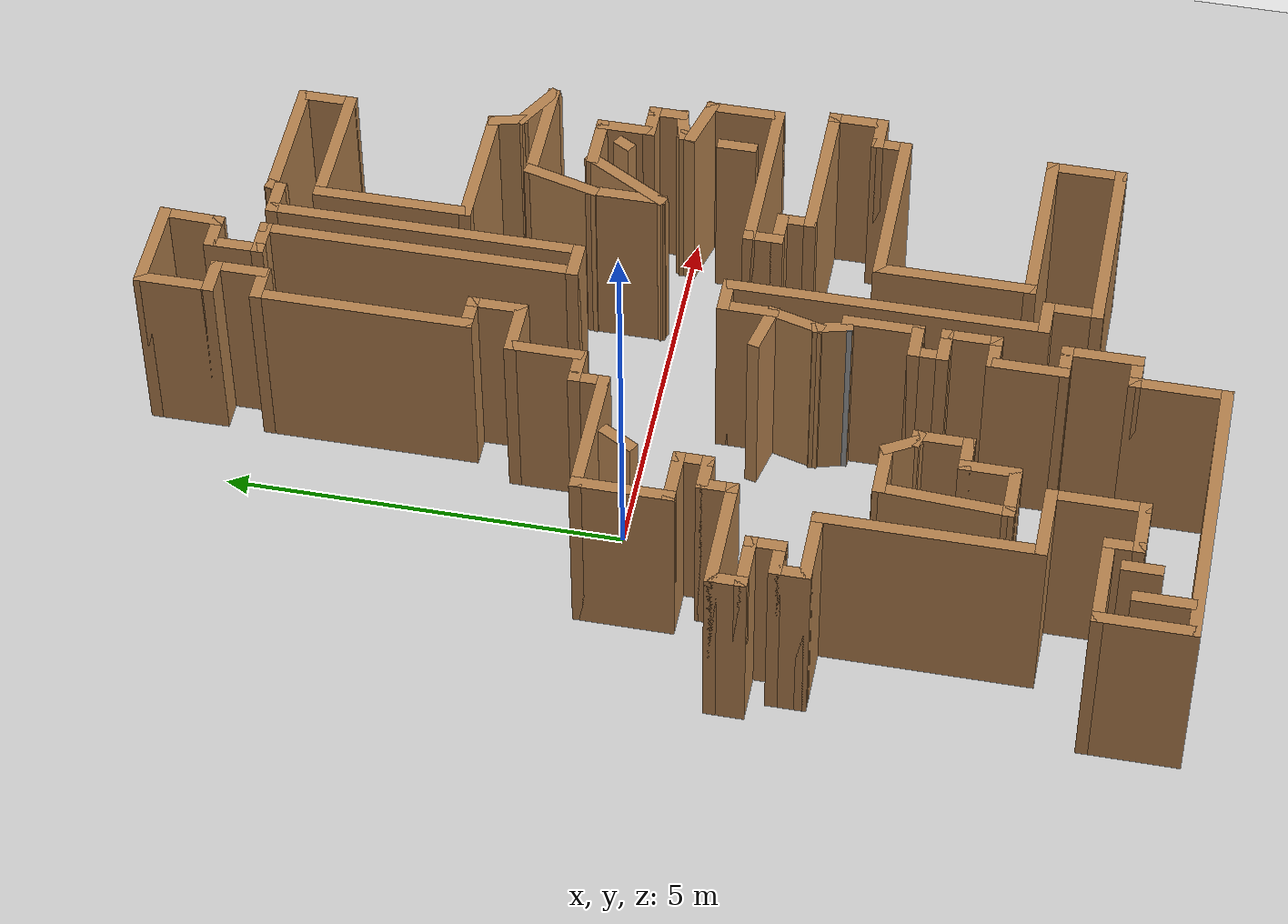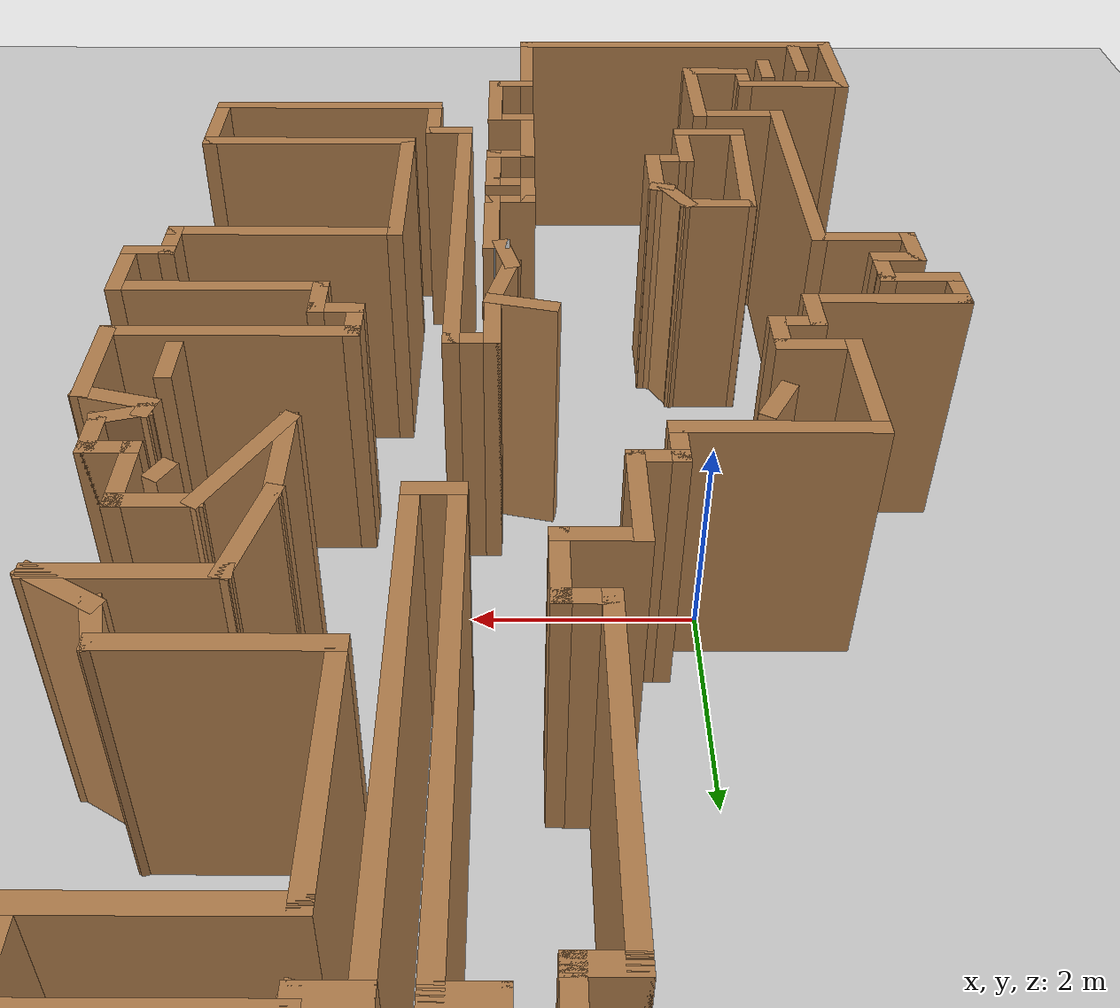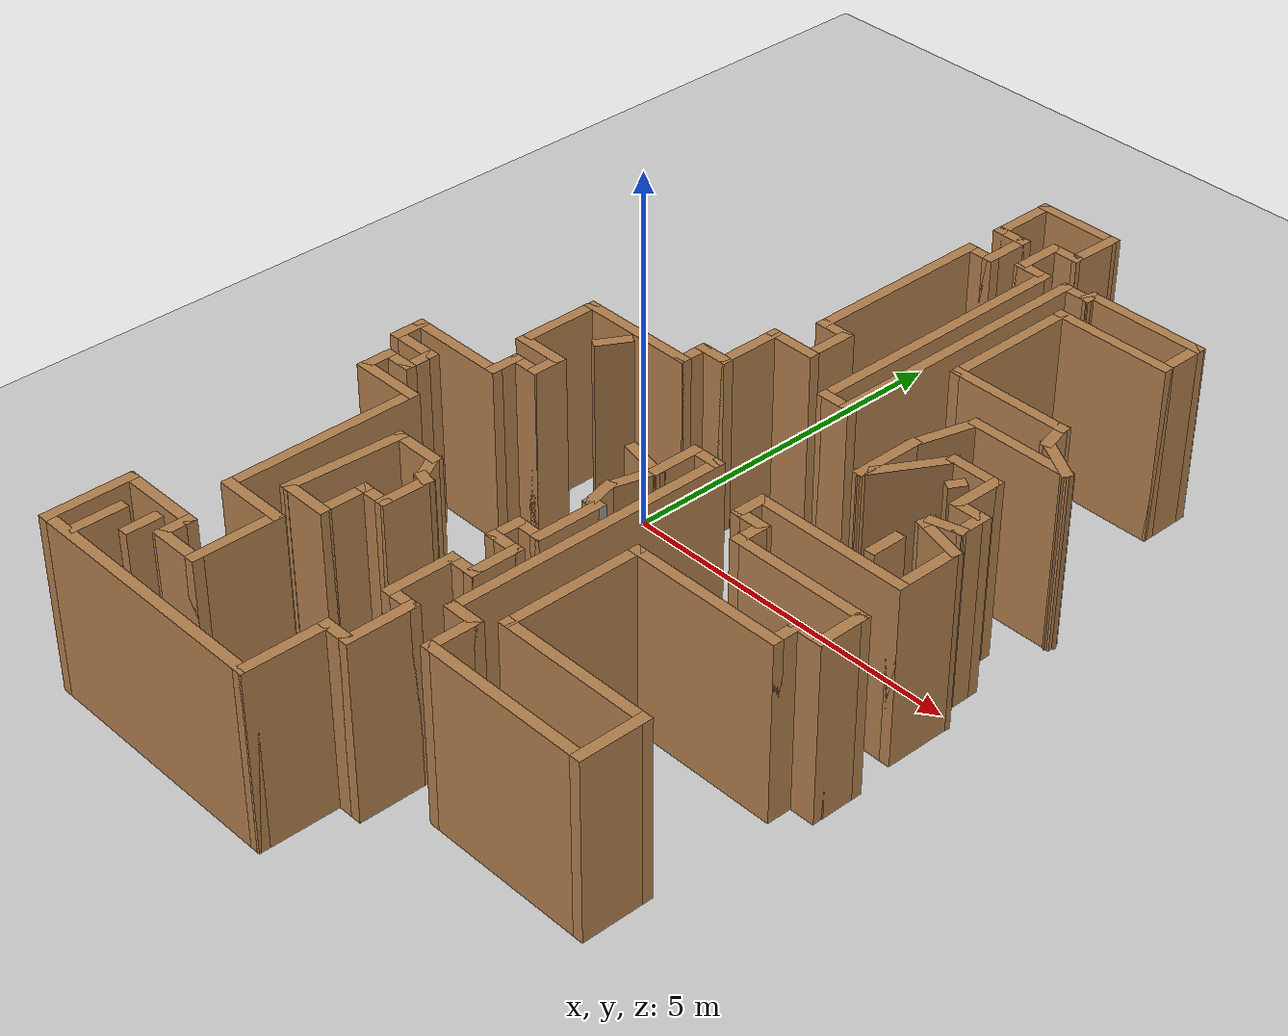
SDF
<sdf version="1.6">
 <world name="default">
  <light name="sun" type="directional">
   <pose>0 0 10 0 -0 0</pose>
   <diffuse>0.8 0.8 0.8 1</diffuse>
   <specular>0.2 0.2 0.2 1</specular>
   <attenuation>
    <range>1000</range>
    <constant>0.9</constant>
    <linear>0.01</linear>
    <quadratic>0.001</quadratic>
   </attenuation>
   <direction>-0.5 0.1 -0.9</direction>
  </light>
  <model name="ground_plane">
   <static>1</static>
   <link name="link">
    <collision name="collision">
     <geometry><plane><normal>0 0 1</normal><size>100 100</size></plane></geometry>
     <surface>
      <contact><collide_bitmask>65535</collide_bitmask></contact>
      <friction><ode><mu>100</mu><mu2>50</mu2></ode></friction>
     </surface>
    </collision>
    <visual name="visual">
     <cast_shadows>0</cast_shadows>
     <geometry><plane><normal>0 0 1</normal><size>100 100</size></plane></geometry>
     <material>
      <script><uri>file://media/materials/scripts/gazebo.material</uri><name>Gazebo/Grey</name></script>
     </material>
    </visual>
   </link>
  </model>
  <gravity>0 0 -9.8</gravity>
  <magnetic_field>6e-06 2.3e-05 -4.2e-05</magnetic_field>
  <atmosphere type="adiabatic"/>
  <physics name="default_physics" default="0" type="ode">
   <max_step_size>0.001</max_step_size>
   <real_time_factor>1</real_time_factor>
   <real_time_update_rate>1000</real_time_update_rate>
  </physics>
  <scene><ambient>0.4 0.4 0.4 1</ambient><background>0.7 0.7 0.7 1</background><shadows>1</shadows></scene>
  <audio><device>default</device></audio>
  <spherical_coordinates>
   <surface_model>EARTH_WGS84</surface_model>
   <latitude_deg>0</latitude_deg>
   <longitude_deg>0</longitude_deg>
   <elevation>0</elevation>
   <heading_deg>0</heading_deg>
  </spherical_coordinates>
  <model name="map_32">
   <pose>1.44168 -0.43788 0 0 -0 0</pose>
   <link name="Wall_10">
    <collision name="Wall_10_Collision">
     <geometry><box><size>0.75 0.15 2.5</size></box></geometry>
     <pose>0 0 1.25 0 -0 0</pose>
    </collision>
    <visual name="Wall_10_Visual">
     <pose>0 0 1.25 0 -0 0</pose>
     <geometry><box><size>0.75 0.15 2.5</size></box></geometry>
     <material>
      <script><uri>file://media/materials/scripts/gazebo.material</uri><name>Gazebo/Wood</name></script>
      <ambient>1 1 1 1</ambient>
     </material>
     <meta><layer>0</layer></meta>
    </visual>
    <pose>-0.432352 1.92407 0 0 -0 3.14159</pose>
   </link>
   <link name="Wall_103">
    <collision name="Wall_103_Collision">
     <geometry><box><size>1.75 0.15 2.5</size></box></geometry>
     <pose>0 0 1.25 0 -0 0</pose>
    </collision>
    <visual name="Wall_103_Visual">
     <pose>0 0 1.25 0 -0 0</pose>
     <geometry><box><size>1.75 0.15 2.5</size></box></geometry>
     <material>
      <script><uri>file://media/materials/scripts/gazebo.material</uri><name>Gazebo/Wood</name></script>
      <ambient>1 1 1 1</ambient>
     </material>
     <meta><layer>0</layer></meta>
    </visual>
    <pose>2.12655 5.39066 0 0 -0 3.14159</pose>
   </link>
   <link name="Wall_104">
    <collision name="Wall_104_Collision">
     <geometry><box><size>0.25 0.15 2.5</size></box></geometry>
     <pose>0 0 1.25 0 -0 0</pose>
    </collision>
    <visual name="Wall_104_Visual">
     <pose>0 0 1.25 0 -0 0</pose>
     <geometry><box><size>0.25 0.15 2.5</size></box></geometry>
     <material>
      <script><uri>file://media/materials/scripts/gazebo.material</uri><name>Gazebo/Wood</name></script>
      <ambient>1 1 1 1</ambient>
     </material>
     <meta><layer>0</layer></meta>
    </visual>
    <pose>1.31361 5.34236 0 0 -0 -1.8326</pose>
   </link>
   <link name="Wall_105">
    <collision name="Wall_105_Collision">
     <geometry><box><size>0.5 0.15 2.5</size></box></geometry>
     <pose>0 0 1.25 0 -0 0</pose>
    </collision>
    <visual name="Wall_105_Visual">
     <pose>0 0 1.25 0 -0 0</pose>
     <geometry><box><size>0.5 0.15 2.5</size></box></geometry>
     <material>
      <script><uri>file://media/materials/scripts/gazebo.material</uri><name>Gazebo/Wood</name></script>
      <ambient>1 1 1 1</ambient>
     </material>
     <meta><layer>0</layer></meta>
    </visual>
    <pose>1.12566 5.29407 0 0 -0 3.14159</pose>
   </link>
   <link name="Wall_106">
    <collision name="Wall_106_Collision">
     <geometry><box><size>4 0.15 2.5</size></box></geometry>
     <pose>0 0 1.25 0 -0 0</pose>
    </collision>
    <visual name="Wall_106_Visual">
     <pose>0 0 1.25 0 -0 0</pose>
     <geometry><box><size>4 0.15 2.5</size></box></geometry>
     <material>
      <script><uri>file://media/materials/scripts/gazebo.material</uri><name>Gazebo/Wood</name></script>
      <ambient>1 1 1 1</ambient>
     </material>
     <meta><layer>0</layer></meta>
    </visual>
    <pose>0.950665 3.36907 0 0 -0 -1.5708</pose>
   </link>
   <link name="Wall_107">
    <collision name="Wall_107_Collision">
     <geometry><box><size>0.5 0.15 2.5</size></box></geometry>
     <pose>0 0 1.25 0 -0 0</pose>
    </collision>
    <visual name="Wall_107_Visual">
     <pose>0 0 1.25 0 -0 0</pose>
     <geometry><box><size>0.5 0.15 2.5</size></box></geometry>
     <material>
      <script><uri>file://media/materials/scripts/gazebo.material</uri><name>Gazebo/Wood</name></script>
      <ambient>1 1 1 1</ambient>
     </material>
     <meta><layer>0</layer></meta>
    </visual>
    <pose>0.775665 1.44407 0 0 -0 3.14159</pose>
   </link>
   <link name="Wall_108">
    <collision name="Wall_108_Collision">
     <geometry><box><size>4 0.15 2.5</size></box></geometry>
     <pose>0 0 1.25 0 -0 0</pose>
    </collision>
    <visual name="Wall_108_Visual">
     <pose>0 0 1.25 0 -0 0</pose>
     <geometry><box><size>4 0.15 2.5</size></box></geometry>
     <material>
      <script><uri>file://media/materials/scripts/gazebo.material</uri><name>Gazebo/Wood</name></script>
      <ambient>1 1 1 1</ambient>
     </material>
     <meta><layer>0</layer></meta>
    </visual>
    <pose>0.600665 3.36907 0 0 -0 1.5708</pose>
   </link>
   <link name="Wall_109">
    <collision name="Wall_109_Collision">
     <geometry><box><size>0.5 0.15 2.5</size></box></geometry>
     <pose>0 0 1.25 0 -0 0</pose>
    </collision>
    <visual name="Wall_109_Visual">
     <pose>0 0 1.25 0 -0 0</pose>
     <geometry><box><size>0.5 0.15 2.5</size></box></geometry>
     <material>
      <script><uri>file://media/materials/scripts/gazebo.material</uri><name>Gazebo/Wood</name></script>
      <ambient>1 1 1 1</ambient>
     </material>
     <meta><layer>0</layer></meta>
    </visual>
    <pose>0.425665 5.29407 0 0 -0 3.14159</pose>
   </link>
   <link name="Wall_11">
    <collision name="Wall_11_Collision">
     <geometry><box><size>1 0.15 2.5</size></box></geometry>
     <pose>0 0 1.25 0 -0 0</pose>
    </collision>
    <visual name="Wall_11_Visual">
     <pose>0 0 1.25 0 -0 0</pose>
     <geometry><box><size>1 0.15 2.5</size></box></geometry>
     <material>
      <script><uri>file://media/materials/scripts/gazebo.material</uri><name>Gazebo/Wood</name></script>
      <ambient>1 1 1 1</ambient>
     </material>
     <meta><layer>0</layer></meta>
    </visual>
    <pose>-0.732352 1.49907 0 0 -0 -1.5708</pose>
   </link>
   <link name="Wall_110">
    <collision name="Wall_110_Collision">
     <geometry><box><size>0.75 0.15 2.5</size></box></geometry>
     <pose>0 0 1.25 0 -0 0</pose>
    </collision>
    <visual name="Wall_110_Visual">
     <pose>0 0 1.25 0 -0 0</pose>
     <geometry><box><size>0.75 0.15 2.5</size></box></geometry>
     <material>
      <script><uri>file://media/materials/scripts/gazebo.material</uri><name>Gazebo/Wood</name></script>
      <ambient>1 1 1 1</ambient>
     </material>
     <meta><layer>0</layer></meta>
    </visual>
    <pose>0.250665 5.59407 0 0 -0 1.5708</pose>
   </link>
   <link name="Wall_111">
    <collision name="Wall_111_Collision">
     <geometry><box><size>0.5 0.15 2.5</size></box></geometry>
     <pose>0 0 1.25 0 -0 0</pose>
    </collision>
    <visual name="Wall_111_Visual">
     <pose>0 0 1.25 0 -0 0</pose>
     <geometry><box><size>0.5 0.15 2.5</size></box></geometry>
     <material>
      <script><uri>file://media/materials/scripts/gazebo.material</uri><name>Gazebo/Wood</name></script>
      <ambient>1 1 1 1</ambient>
     </material>
     <meta><layer>0</layer></meta>
    </visual>
    <pose>0.425665 5.89407 0 0 -0 0</pose>
   </link>
   <link name="Wall_112">
    <collision name="Wall_112_Collision">
     <geometry><box><size>0.830221 0.15 2.5</size></box></geometry>
     <pose>0 0 1.25 0 -0 0</pose>
    </collision>
    <visual name="Wall_112_Visual">
     <pose>0 0 1.25 0 -0 0</pose>
     <geometry><box><size>0.830221 0.15 2.5</size></box></geometry>
     <material>
      <script><uri>file://media/materials/scripts/gazebo.material</uri><name>Gazebo/Wood</name></script>
      <ambient>1 1 1 1</ambient>
     </material>
     <meta><layer>0</layer></meta>
    </visual>
    <pose>0.609156 6.23407 0 0 -0 1.54583</pose>
   </link>
   <link name="Wall_116">
    <collision name="Wall_116_Collision">
     <geometry><box><size>0.5 0.15 2.5</size></box></geometry>
     <pose>0 0 1.25 0 -0 0</pose>
    </collision>
    <visual name="Wall_116_Visual">
     <pose>0 0 1.25 0 -0 0</pose>
     <geometry><box><size>0.5 0.15 2.5</size></box></geometry>
     <material>
      <script><uri>file://media/materials/scripts/gazebo.material</uri><name>Gazebo/Wood</name></script>
      <ambient>1 1 1 1</ambient>
     </material>
     <meta><layer>0</layer></meta>
    </visual>
    <pose>3.06584 -0.141038 0 0 -0 1.5708</pose>
   </link>
   <link name="Wall_119">
    <collision name="Wall_119_Collision">
     <geometry><box><size>0.25 0.15 2.5</size></box></geometry>
     <pose>0 0 1.25 0 -0 0</pose>
    </collision>
    <visual name="Wall_119_Visual">
     <pose>0 0 1.25 0 -0 0</pose>
     <geometry><box><size>0.25 0.15 2.5</size></box></geometry>
     <material>
      <script><uri>file://media/materials/scripts/gazebo.material</uri><name>Gazebo/Wood</name></script>
      <ambient>1 1 1 1</ambient>
     </material>
     <meta><layer>0</layer></meta>
    </visual>
    <pose>2.83971 1.24975 0 0 -0 -2.0944</pose>
   </link>
   <link name="Wall_121">
    <collision name="Wall_121_Collision">
     <geometry><box><size>0.5 0.15 2.5</size></box></geometry>
     <pose>0 0 1.25 0 -0 0</pose>
    </collision>
    <visual name="Wall_121_Visual">
     <pose>0 0 1.25 0 -0 0</pose>
     <geometry><box><size>0.5 0.15 2.5</size></box></geometry>
     <material>
      <script><uri>file://media/materials/scripts/gazebo.material</uri><name>Gazebo/Wood</name></script>
      <ambient>1 1 1 1</ambient>
     </material>
     <meta><layer>0</layer></meta>
    </visual>
    <pose>-1.92937 0.377178 0 0 -0 -2.0944</pose>
   </link>
   <link name="Wall_123">
    <collision name="Wall_123_Collision">
     <geometry><box><size>0.678088 0.15 2.5</size></box></geometry>
     <pose>0 0 1.25 0 -0 0</pose>
    </collision>
    <visual name="Wall_123_Visual">
     <pose>0 0 1.25 0 -0 0</pose>
     <geometry><box><size>0.678088 0.15 2.5</size></box></geometry>
     <material>
      <script><uri>file://media/materials/scripts/gazebo.material</uri><name>Gazebo/Wood</name></script>
      <ambient>1 1 1 1</ambient>
     </material>
     <meta><layer>0</layer></meta>
    </visual>
    <pose>0.125069 -0.998927 0 0 -0 -0.226782</pose>
   </link>
   <link name="Wall_130">
    <collision name="Wall_130_Collision">
     <geometry><box><size>0.75 0.15 2.5</size></box></geometry>
     <pose>0 0 1.25 0 -0 0</pose>
    </collision>
    <visual name="Wall_130_Visual">
     <pose>0 0 1.25 0 -0 0</pose>
     <geometry><box><size>0.75 0.15 2.5</size></box></geometry>
     <material>
      <script><uri>file://media/materials/scripts/gazebo.material</uri><name>Gazebo/Wood</name></script>
      <ambient>1 1 1 1</ambient>
     </material>
     <meta><layer>0</layer></meta>
    </visual>
    <pose>-1.8838 -4.27841 0 0 -0 0</pose>
   </link>
   <link name="Wall_131">
    <collision name="Wall_131_Collision">
     <geometry><box><size>0.75 0.15 2.5</size></box></geometry>
     <pose>0 0 1.25 0 -0 0</pose>
    </collision>
    <visual name="Wall_131_Visual">
     <pose>0 0 1.25 0 -0 0</pose>
     <geometry><box><size>0.75 0.15 2.5</size></box></geometry>
     <material>
      <script><uri>file://media/materials/scripts/gazebo.material</uri><name>Gazebo/Wood</name></script>
      <ambient>1 1 1 1</ambient>
     </material>
     <meta><layer>0</layer></meta>
    </visual>
    <pose>-1.5838 -3.97841 0 0 -0 1.5708</pose>
   </link>
   <link name="Wall_132">
    <collision name="Wall_132_Collision">
     <geometry><box><size>0.5 0.15 2.5</size></box></geometry>
     <pose>0 0 1.25 0 -0 0</pose>
    </collision>
    <visual name="Wall_132_Visual">
     <pose>0 0 1.25 0 -0 0</pose>
     <geometry><box><size>0.5 0.15 2.5</size></box></geometry>
     <material>
      <script><uri>file://media/materials/scripts/gazebo.material</uri><name>Gazebo/Wood</name></script>
      <ambient>1 1 1 1</ambient>
     </material>
     <meta><layer>0</layer></meta>
    </visual>
    <pose>-1.4088 -3.67841 0 0 -0 0</pose>
   </link>
   <link name="Wall_133">
    <collision name="Wall_133_Collision">
     <geometry><box><size>0.75 0.15 2.5</size></box></geometry>
     <pose>0 0 1.25 0 -0 0</pose>
    </collision>
    <visual name="Wall_133_Visual">
     <pose>0 0 1.25 0 -0 0</pose>
     <geometry><box><size>0.75 0.15 2.5</size></box></geometry>
     <material>
      <script><uri>file://media/materials/scripts/gazebo.material</uri><name>Gazebo/Wood</name></script>
      <ambient>1 1 1 1</ambient>
     </material>
     <meta><layer>0</layer></meta>
    </visual>
    <pose>-1.2338 -3.37841 0 0 -0 1.5708</pose>
   </link>
   <link name="Wall_134">
    <collision name="Wall_134_Collision">
     <geometry><box><size>0.25 0.15 2.5</size></box></geometry>
     <pose>0 0 1.25 0 -0 0</pose>
    </collision>
    <visual name="Wall_134_Visual">
     <pose>0 0 1.25 0 -0 0</pose>
     <geometry><box><size>0.25 0.15 2.5</size></box></geometry>
     <material>
      <script><uri>file://media/materials/scripts/gazebo.material</uri><name>Gazebo/Wood</name></script>
      <ambient>1 1 1 1</ambient>
     </material>
     <meta><layer>0</layer></meta>
    </visual>
    <pose>-1.28209 -3.06547 0 0 -0 2.87979</pose>
   </link>
   <link name="Wall_135">
    <collision name="Wall_135_Collision">
     <geometry><box><size>0.5 0.15 2.5</size></box></geometry>
     <pose>0 0 1.25 0 -0 0</pose>
    </collision>
    <visual name="Wall_135_Visual">
     <pose>0 0 1.25 0 -0 0</pose>
     <geometry><box><size>0.5 0.15 2.5</size></box></geometry>
     <material>
      <script><uri>file://media/materials/scripts/gazebo.material</uri><name>Gazebo/Wood</name></script>
      <ambient>1 1 1 1</ambient>
     </material>
     <meta><layer>0</layer></meta>
    </visual>
    <pose>-1.41789 -2.90097 0 0 -0 2.0944</pose>
   </link>
   <link name="Wall_136">
    <collision name="Wall_136_Collision">
     <geometry><box><size>0.75 0.15 2.5</size></box></geometry>
     <pose>0 0 1.25 0 -0 0</pose>
    </collision>
    <visual name="Wall_136_Visual">
     <pose>0 0 1.25 0 -0 0</pose>
     <geometry><box><size>0.75 0.15 2.5</size></box></geometry>
     <material>
      <script><uri>file://media/materials/scripts/gazebo.material</uri><name>Gazebo/Wood</name></script>
      <ambient>1 1 1 1</ambient>
     </material>
     <meta><layer>0</layer></meta>
    </visual>
    <pose>-1.80539 -2.74942 0 0 -0 3.14159</pose>
   </link>
   <link name="Wall_137">
    <collision name="Wall_137_Collision">
     <geometry><box><size>1.681 0.15 2.5</size></box></geometry>
     <pose>0 0 1.25 0 -0 0</pose>
    </collision>
    <visual name="Wall_137_Visual">
     <pose>0 0 1.25 0 -0 0</pose>
     <geometry><box><size>1.681 0.15 2.5</size></box></geometry>
     <material>
      <script><uri>file://media/materials/scripts/gazebo.material</uri><name>Gazebo/Wood</name></script>
      <ambient>1 1 1 1</ambient>
     </material>
     <meta><layer>0</layer></meta>
    </visual>
    <pose>-2.14459 -3.51392 0 0 -0 -1.62203</pose>
   </link>
   <link name="Wall_139">
    <collision name="Wall_139_Collision">
     <geometry><box><size>0.75 0.15 2.5</size></box></geometry>
     <pose>0 0 1.25 0 -0 0</pose>
    </collision>
    <visual name="Wall_139_Visual">
     <pose>0 0 1.25 0 -0 0</pose>
     <geometry><box><size>0.75 0.15 2.5</size></box></geometry>
     <material>
      <script><uri>file://media/materials/scripts/gazebo.material</uri><name>Gazebo/Wood</name></script>
      <ambient>1 1 1 1</ambient>
     </material>
     <meta><layer>0</layer></meta>
    </visual>
    <pose>-3.14925 -6.1875 0 0 -0 -1.5708</pose>
   </link>
   <link name="Wall_14">
    <collision name="Wall_14_Collision">
     <geometry><box><size>0.5 0.15 2.5</size></box></geometry>
     <pose>0 0 1.25 0 -0 0</pose>
    </collision>
    <visual name="Wall_14_Visual">
     <pose>0 0 1.25 0 -0 0</pose>
     <geometry><box><size>0.5 0.15 2.5</size></box></geometry>
     <material>
      <script><uri>file://media/materials/scripts/gazebo.material</uri><name>Gazebo/Wood</name></script>
      <ambient>1 1 1 1</ambient>
     </material>
     <meta><layer>0</layer></meta>
    </visual>
    <pose>-0.907352 1.07407 0 0 -0 3.14159</pose>
   </link>
   <link name="Wall_142">
    <collision name="Wall_142_Collision">
     <geometry><box><size>0.5 0.15 2.5</size></box></geometry>
     <pose>0 0 1.25 0 -0 0</pose>
    </collision>
    <visual name="Wall_142_Visual">
     <pose>0 0 1.25 0 -0 0</pose>
     <geometry><box><size>0.5 0.15 2.5</size></box></geometry>
     <material>
      <script><uri>file://media/materials/scripts/gazebo.material</uri><name>Gazebo/Wood</name></script>
      <ambient>1 1 1 1</ambient>
     </material>
     <meta><layer>0</layer></meta>
    </visual>
    <pose>-2.72686 -5.89352 0 0 -0 1.5708</pose>
   </link>
   <link name="Wall_15">
    <collision name="Wall_15_Collision">
     <geometry><box><size>0.5 0.15 2.5</size></box></geometry>
     <pose>0 0 1.25 0 -0 0</pose>
    </collision>
    <visual name="Wall_15_Visual">
     <pose>0 0 1.25 0 -0 0</pose>
     <geometry><box><size>0.5 0.15 2.5</size></box></geometry>
     <material>
      <script><uri>file://media/materials/scripts/gazebo.material</uri><name>Gazebo/Wood</name></script>
      <ambient>1 1 1 1</ambient>
     </material>
     <meta><layer>0</layer></meta>
    </visual>
    <pose>-1.08235 0.899075 0 0 -0 -1.5708</pose>
   </link>
   <link name="Wall_18">
    <collision name="Wall_18_Collision">
     <geometry><box><size>1.75 0.15 2.5</size></box></geometry>
     <pose>0 0 1.25 0 -0 0</pose>
    </collision>
    <visual name="Wall_18_Visual">
     <pose>0 0 1.25 0 -0 0</pose>
     <geometry><box><size>1.75 0.15 2.5</size></box></geometry>
     <material>
      <script><uri>file://media/materials/scripts/gazebo.material</uri><name>Gazebo/Wood</name></script>
      <ambient>1 1 1 1</ambient>
     </material>
     <meta><layer>0</layer></meta>
    </visual>
    <pose>-1.88235 0.724075 0 0 -0 3.14159</pose>
   </link>
   <link name="Wall_19">
    <collision name="Wall_19_Collision">
     <geometry><box><size>1.25 0.15 2.5</size></box></geometry>
     <pose>0 0 1.25 0 -0 0</pose>
    </collision>
    <visual name="Wall_19_Visual">
     <pose>0 0 1.25 0 -0 0</pose>
     <geometry><box><size>1.25 0.15 2.5</size></box></geometry>
     <material>
      <script><uri>file://media/materials/scripts/gazebo.material</uri><name>Gazebo/Wood</name></script>
      <ambient>1 1 1 1</ambient>
     </material>
     <meta><layer>0</layer></meta>
    </visual>
    <pose>-2.68235 0.174075 0 0 -0 -1.5708</pose>
   </link>
   <link name="Wall_2">
    <collision name="Wall_2_Collision">
     <geometry><box><size>1.25 0.15 2.5</size></box></geometry>
     <pose>0 0 1.25 0 -0 0</pose>
    </collision>
    <visual name="Wall_2_Visual">
     <pose>0 0 1.25 0 -0 0</pose>
     <geometry><box><size>1.25 0.15 2.5</size></box></geometry>
     <material>
      <script><uri>file://media/materials/scripts/gazebo.material</uri><name>Gazebo/Wood</name></script>
      <ambient>1 1 1 1</ambient>
     </material>
     <meta><layer>0</layer></meta>
    </visual>
    <pose>0.067648 6.57408 0 0 -0 3.14159</pose>
   </link>
   <link name="Wall_20">
    <collision name="Wall_20_Collision">
     <geometry><box><size>0.75 0.15 2.5</size></box></geometry>
     <pose>0 0 1.25 0 -0 0</pose>
    </collision>
    <visual name="Wall_20_Visual">
     <pose>0 0 1.25 0 -0 0</pose>
     <geometry><box><size>0.75 0.15 2.5</size></box></geometry>
     <material>
      <script><uri>file://media/materials/scripts/gazebo.material</uri><name>Gazebo/Wood</name></script>
      <ambient>1 1 1 1</ambient>
     </material>
     <meta><layer>0</layer></meta>
    </visual>
    <pose>-2.38235 -0.375925 0 0 -0 0</pose>
   </link>
   <link name="Wall_21">
    <collision name="Wall_21_Collision">
     <geometry><box><size>0.5 0.15 2.5</size></box></geometry>
     <pose>0 0 1.25 0 -0 0</pose>
    </collision>
    <visual name="Wall_21_Visual">
     <pose>0 0 1.25 0 -0 0</pose>
     <geometry><box><size>0.5 0.15 2.5</size></box></geometry>
     <material>
      <script><uri>file://media/materials/scripts/gazebo.material</uri><name>Gazebo/Wood</name></script>
      <ambient>1 1 1 1</ambient>
     </material>
     <meta><layer>0</layer></meta>
    </visual>
    <pose>-2.08235 -0.550925 0 0 -0 -1.5708</pose>
   </link>
   <link name="Wall_22">
    <collision name="Wall_22_Collision">
     <geometry><box><size>0.5 0.15 2.5</size></box></geometry>
     <pose>0 0 1.25 0 -0 0</pose>
    </collision>
    <visual name="Wall_22_Visual">
     <pose>0 0 1.25 0 -0 0</pose>
     <geometry><box><size>0.5 0.15 2.5</size></box></geometry>
     <material>
      <script><uri>file://media/materials/scripts/gazebo.material</uri><name>Gazebo/Wood</name></script>
      <ambient>1 1 1 1</ambient>
     </material>
     <meta><layer>0</layer></meta>
    </visual>
    <pose>-2.25735 -0.725925 0 0 -0 3.14159</pose>
   </link>
   <link name="Wall_23">
    <collision name="Wall_23_Collision">
     <geometry><box><size>0.5 0.15 2.5</size></box></geometry>
     <pose>0 0 1.25 0 -0 0</pose>
    </collision>
    <visual name="Wall_23_Visual">
     <pose>0 0 1.25 0 -0 0</pose>
     <geometry><box><size>0.5 0.15 2.5</size></box></geometry>
     <material>
      <script><uri>file://media/materials/scripts/gazebo.material</uri><name>Gazebo/Wood</name></script>
      <ambient>1 1 1 1</ambient>
     </material>
     <meta><layer>0</layer></meta>
    </visual>
    <pose>-2.43235 -0.900925 0 0 -0 -1.5708</pose>
   </link>
   <link name="Wall_24">
    <collision name="Wall_24_Collision">
     <geometry><box><size>1.5 0.15 2.5</size></box></geometry>
     <pose>0 0 1.25 0 -0 0</pose>
    </collision>
    <visual name="Wall_24_Visual">
     <pose>0 0 1.25 0 -0 0</pose>
     <geometry><box><size>1.5 0.15 2.5</size></box></geometry>
     <material>
      <script><uri>file://media/materials/scripts/gazebo.material</uri><name>Gazebo/Wood</name></script>
      <ambient>1 1 1 1</ambient>
     </material>
     <meta><layer>0</layer></meta>
    </visual>
    <pose>-3.10735 -1.07593 0 0 -0 3.14159</pose>
   </link>
   <link name="Wall_27">
    <collision name="Wall_27_Collision">
     <geometry><box><size>0.5 0.15 2.5</size></box></geometry>
     <pose>0 0 1.25 0 -0 0</pose>
    </collision>
    <visual name="Wall_27_Visual">
     <pose>0 0 1.25 0 -0 0</pose>
     <geometry><box><size>0.5 0.15 2.5</size></box></geometry>
     <material>
      <script><uri>file://media/materials/scripts/gazebo.material</uri><name>Gazebo/Wood</name></script>
      <ambient>1 1 1 1</ambient>
     </material>
     <meta><layer>0</layer></meta>
    </visual>
    <pose>-3.78235 -1.25093 0 0 -0 -1.5708</pose>
   </link>
   <link name="Wall_28">
    <collision name="Wall_28_Collision">
     <geometry><box><size>0.75 0.15 2.5</size></box></geometry>
     <pose>0 0 1.25 0 -0 0</pose>
    </collision>
    <visual name="Wall_28_Visual">
     <pose>0 0 1.25 0 -0 0</pose>
     <geometry><box><size>0.75 0.15 2.5</size></box></geometry>
     <material>
      <script><uri>file://media/materials/scripts/gazebo.material</uri><name>Gazebo/Wood</name></script>
      <ambient>1 1 1 1</ambient>
     </material>
     <meta><layer>0</layer></meta>
    </visual>
    <pose>-3.48235 -1.42593 0 0 -0 0</pose>
   </link>
   <link name="Wall_29">
    <collision name="Wall_29_Collision">
     <geometry><box><size>0.5 0.15 2.5</size></box></geometry>
     <pose>0 0 1.25 0 -0 0</pose>
    </collision>
    <visual name="Wall_29_Visual">
     <pose>0 0 1.25 0 -0 0</pose>
     <geometry><box><size>0.5 0.15 2.5</size></box></geometry>
     <material>
      <script><uri>file://media/materials/scripts/gazebo.material</uri><name>Gazebo/Wood</name></script>
      <ambient>1 1 1 1</ambient>
     </material>
     <meta><layer>0</layer></meta>
    </visual>
    <pose>-3.18235 -1.60092 0 0 -0 -1.5708</pose>
   </link>
   <link name="Wall_3">
    <collision name="Wall_3_Collision">
     <geometry><box><size>1 0.15 2.5</size></box></geometry>
     <pose>0 0 1.25 0 -0 0</pose>
    </collision>
    <visual name="Wall_3_Visual">
     <pose>0 0 1.25 0 -0 0</pose>
     <geometry><box><size>1 0.15 2.5</size></box></geometry>
     <material>
      <script><uri>file://media/materials/scripts/gazebo.material</uri><name>Gazebo/Wood</name></script>
      <ambient>1 1 1 1</ambient>
     </material>
     <meta><layer>0</layer></meta>
    </visual>
    <pose>-0.482352 6.14908 0 0 -0 -1.5708</pose>
   </link>
   <link name="Wall_30">
    <collision name="Wall_30_Collision">
     <geometry><box><size>0.5 0.15 2.5</size></box></geometry>
     <pose>0 0 1.25 0 -0 0</pose>
    </collision>
    <visual name="Wall_30_Visual">
     <pose>0 0 1.25 0 -0 0</pose>
     <geometry><box><size>0.5 0.15 2.5</size></box></geometry>
     <material>
      <script><uri>file://media/materials/scripts/gazebo.material</uri><name>Gazebo/Wood</name></script>
      <ambient>1 1 1 1</ambient>
     </material>
     <meta><layer>0</layer></meta>
    </visual>
    <pose>-3.35735 -1.77592 0 0 -0 3.14159</pose>
   </link>
   <link name="Wall_31">
    <collision name="Wall_31_Collision">
     <geometry><box><size>0.5 0.15 2.5</size></box></geometry>
     <pose>0 0 1.25 0 -0 0</pose>
    </collision>
    <visual name="Wall_31_Visual">
     <pose>0 0 1.25 0 -0 0</pose>
     <geometry><box><size>0.5 0.15 2.5</size></box></geometry>
     <material>
      <script><uri>file://media/materials/scripts/gazebo.material</uri><name>Gazebo/Wood</name></script>
      <ambient>1 1 1 1</ambient>
     </material>
     <meta><layer>0</layer></meta>
    </visual>
    <pose>-3.53235 -1.95093 0 0 -0 -1.5708</pose>
   </link>
   <link name="Wall_32">
    <collision name="Wall_32_Collision">
     <geometry><box><size>1 0.15 2.5</size></box></geometry>
     <pose>0 0 1.25 0 -0 0</pose>
    </collision>
    <visual name="Wall_32_Visual">
     <pose>0 0 1.25 0 -0 0</pose>
     <geometry><box><size>1 0.15 2.5</size></box></geometry>
     <material>
      <script><uri>file://media/materials/scripts/gazebo.material</uri><name>Gazebo/Wood</name></script>
      <ambient>1 1 1 1</ambient>
     </material>
     <meta><layer>0</layer></meta>
    </visual>
    <pose>-3.10735 -2.12593 0 0 -0 0</pose>
   </link>
   <link name="Wall_33">
    <collision name="Wall_33_Collision">
     <geometry><box><size>2.75 0.15 2.5</size></box></geometry>
     <pose>0 0 1.25 0 -0 0</pose>
    </collision>
    <visual name="Wall_33_Visual">
     <pose>0 0 1.25 0 -0 0</pose>
     <geometry><box><size>2.75 0.15 2.5</size></box></geometry>
     <material>
      <script><uri>file://media/materials/scripts/gazebo.material</uri><name>Gazebo/Wood</name></script>
      <ambient>1 1 1 1</ambient>
     </material>
     <meta><layer>0</layer></meta>
    </visual>
    <pose>-2.68235 -3.42592 0 0 -0 -1.5708</pose>
   </link>
   <link name="Wall_34">
    <collision name="Wall_34_Collision">
     <geometry><box><size>1 0.15 2.5</size></box></geometry>
     <pose>0 0 1.25 0 -0 0</pose>
    </collision>
    <visual name="Wall_34_Visual">
     <pose>0 0 1.25 0 -0 0</pose>
     <geometry><box><size>1 0.15 2.5</size></box></geometry>
     <material>
      <script><uri>file://media/materials/scripts/gazebo.material</uri><name>Gazebo/Wood</name></script>
      <ambient>1 1 1 1</ambient>
     </material>
     <meta><layer>0</layer></meta>
    </visual>
    <pose>-2.25735 -4.72593 0 0 -0 0</pose>
   </link>
   <link name="Wall_37">
    <collision name="Wall_37_Collision">
     <geometry><box><size>1.25 0.15 2.5</size></box></geometry>
     <pose>0 0 1.25 0 -0 0</pose>
    </collision>
    <visual name="Wall_37_Visual">
     <pose>0 0 1.25 0 -0 0</pose>
     <geometry><box><size>1.25 0.15 2.5</size></box></geometry>
     <material>
      <script><uri>file://media/materials/scripts/gazebo.material</uri><name>Gazebo/Wood</name></script>
      <ambient>1 1 1 1</ambient>
     </material>
     <meta><layer>0</layer></meta>
    </visual>
    <pose>-1.83235 -5.27592 0 0 -0 -1.5708</pose>
   </link>
   <link name="Wall_4">
    <collision name="Wall_4_Collision">
     <geometry><box><size>0.5 0.15 2.5</size></box></geometry>
     <pose>0 0 1.25 0 -0 0</pose>
    </collision>
    <visual name="Wall_4_Visual">
     <pose>0 0 1.25 0 -0 0</pose>
     <geometry><box><size>0.5 0.15 2.5</size></box></geometry>
     <material>
      <script><uri>file://media/materials/scripts/gazebo.material</uri><name>Gazebo/Wood</name></script>
      <ambient>1 1 1 1</ambient>
     </material>
     <meta><layer>0</layer></meta>
    </visual>
    <pose>-0.307352 5.72408 0 0 -0 0</pose>
   </link>
   <link name="Wall_40">
    <collision name="Wall_40_Collision">
     <geometry><box><size>0.75 0.15 2.5</size></box></geometry>
     <pose>0 0 1.25 0 -0 0</pose>
    </collision>
    <visual name="Wall_40_Visual">
     <pose>0 0 1.25 0 -0 0</pose>
     <geometry><box><size>0.75 0.15 2.5</size></box></geometry>
     <material>
      <script><uri>file://media/materials/scripts/gazebo.material</uri><name>Gazebo/Wood</name></script>
      <ambient>1 1 1 1</ambient>
     </material>
     <meta><layer>0</layer></meta>
    </visual>
    <pose>-2.13235 -5.82592 0 0 -0 3.14159</pose>
   </link>
   <link name="Wall_41">
    <collision name="Wall_41_Collision">
     <geometry><box><size>0.5 0.15 2.5</size></box></geometry>
     <pose>0 0 1.25 0 -0 0</pose>
    </collision>
    <visual name="Wall_41_Visual">
     <pose>0 0 1.25 0 -0 0</pose>
     <geometry><box><size>0.5 0.15 2.5</size></box></geometry>
     <material>
      <script><uri>file://media/materials/scripts/gazebo.material</uri><name>Gazebo/Wood</name></script>
      <ambient>1 1 1 1</ambient>
     </material>
     <meta><layer>0</layer></meta>
    </visual>
    <pose>-2.43235 -5.65092 0 0 -0 1.5708</pose>
   </link>
   <link name="Wall_42">
    <collision name="Wall_42_Collision">
     <geometry><box><size>1.25 0.15 2.5</size></box></geometry>
     <pose>0 0 1.25 0 -0 0</pose>
    </collision>
    <visual name="Wall_42_Visual">
     <pose>0 0 1.25 0 -0 0</pose>
     <geometry><box><size>1.25 0.15 2.5</size></box></geometry>
     <material>
      <script><uri>file://media/materials/scripts/gazebo.material</uri><name>Gazebo/Wood</name></script>
      <ambient>1 1 1 1</ambient>
     </material>
     <meta><layer>0</layer></meta>
    </visual>
    <pose>-2.98235 -5.47593 0 0 -0 3.14159</pose>
   </link>
   <link name="Wall_43">
    <collision name="Wall_43_Collision">
     <geometry><box><size>1.25 0.15 2.5</size></box></geometry>
     <pose>0 0 1.25 0 -0 0</pose>
    </collision>
    <visual name="Wall_43_Visual">
     <pose>0 0 1.25 0 -0 0</pose>
     <geometry><box><size>1.25 0.15 2.5</size></box></geometry>
     <material>
      <script><uri>file://media/materials/scripts/gazebo.material</uri><name>Gazebo/Wood</name></script>
      <ambient>1 1 1 1</ambient>
     </material>
     <meta><layer>0</layer></meta>
    </visual>
    <pose>-3.53235 -6.02592 0 0 -0 -1.5708</pose>
   </link>
   <link name="Wall_44">
    <collision name="Wall_44_Collision">
     <geometry><box><size>3.75 0.15 2.5</size></box></geometry>
     <pose>0 0 1.25 0 -0 0</pose>
    </collision>
    <visual name="Wall_44_Visual">
     <pose>0 0 1.25 0 -0 0</pose>
     <geometry><box><size>3.75 0.15 2.5</size></box></geometry>
     <material>
      <script><uri>file://media/materials/scripts/gazebo.material</uri><name>Gazebo/Wood</name></script>
      <ambient>1 1 1 1</ambient>
     </material>
     <meta><layer>0</layer></meta>
    </visual>
    <pose>-1.73235 -6.57592 0 0 -0 0</pose>
   </link>
   <link name="Wall_45">
    <collision name="Wall_45_Collision">
     <geometry><box><size>1.25 0.15 2.5</size></box></geometry>
     <pose>0 0 1.25 0 -0 0</pose>
    </collision>
    <visual name="Wall_45_Visual">
     <pose>0 0 1.25 0 -0 0</pose>
     <geometry><box><size>1.25 0.15 2.5</size></box></geometry>
     <material>
      <script><uri>file://media/materials/scripts/gazebo.material</uri><name>Gazebo/Wood</name></script>
      <ambient>1 1 1 1</ambient>
     </material>
     <meta><layer>0</layer></meta>
    </visual>
    <pose>0.067648 -6.02592 0 0 -0 1.5708</pose>
   </link>
   <link name="Wall_46">
    <collision name="Wall_46_Collision">
     <geometry><box><size>0.5 0.15 2.5</size></box></geometry>
     <pose>0 0 1.25 0 -0 0</pose>
    </collision>
    <visual name="Wall_46_Visual">
     <pose>0 0 1.25 0 -0 0</pose>
     <geometry><box><size>0.5 0.15 2.5</size></box></geometry>
     <material>
      <script><uri>file://media/materials/scripts/gazebo.material</uri><name>Gazebo/Wood</name></script>
      <ambient>1 1 1 1</ambient>
     </material>
     <meta><layer>0</layer></meta>
    </visual>
    <pose>0.242648 -5.47593 0 0 -0 0</pose>
   </link>
   <link name="Wall_47">
    <collision name="Wall_47_Collision">
     <geometry><box><size>1 0.15 2.5</size></box></geometry>
     <pose>0 0 1.25 0 -0 0</pose>
    </collision>
    <visual name="Wall_47_Visual">
     <pose>0 0 1.25 0 -0 0</pose>
     <geometry><box><size>1 0.15 2.5</size></box></geometry>
     <material>
      <script><uri>file://media/materials/scripts/gazebo.material</uri><name>Gazebo/Wood</name></script>
      <ambient>1 1 1 1</ambient>
     </material>
     <meta><layer>0</layer></meta>
    </visual>
    <pose>0.417648 -5.05093 0 0 -0 1.5708</pose>
   </link>
   <link name="Wall_48">
    <collision name="Wall_48_Collision">
     <geometry><box><size>0.5 0.15 2.5</size></box></geometry>
     <pose>0 0 1.25 0 -0 0</pose>
    </collision>
    <visual name="Wall_48_Visual">
     <pose>0 0 1.25 0 -0 0</pose>
     <geometry><box><size>0.5 0.15 2.5</size></box></geometry>
     <material>
      <script><uri>file://media/materials/scripts/gazebo.material</uri><name>Gazebo/Wood</name></script>
      <ambient>1 1 1 1</ambient>
     </material>
     <meta><layer>0</layer></meta>
    </visual>
    <pose>0.242648 -4.62592 0 0 -0 3.14159</pose>
   </link>
   <link name="Wall_49">
    <collision name="Wall_49_Collision">
     <geometry><box><size>1 0.15 2.5</size></box></geometry>
     <pose>0 0 1.25 0 -0 0</pose>
    </collision>
    <visual name="Wall_49_Visual">
     <pose>0 0 1.25 0 -0 0</pose>
     <geometry><box><size>1 0.15 2.5</size></box></geometry>
     <material>
      <script><uri>file://media/materials/scripts/gazebo.material</uri><name>Gazebo/Wood</name></script>
      <ambient>1 1 1 1</ambient>
     </material>
     <meta><layer>0</layer></meta>
    </visual>
    <pose>0.067648 -4.20092 0 0 -0 1.5708</pose>
   </link>
   <link name="Wall_5">
    <collision name="Wall_5_Collision">
     <geometry><box><size>0.75 0.15 2.5</size></box></geometry>
     <pose>0 0 1.25 0 -0 0</pose>
    </collision>
    <visual name="Wall_5_Visual">
     <pose>0 0 1.25 0 -0 0</pose>
     <geometry><box><size>0.75 0.15 2.5</size></box></geometry>
     <material>
      <script><uri>file://media/materials/scripts/gazebo.material</uri><name>Gazebo/Wood</name></script>
      <ambient>1 1 1 1</ambient>
     </material>
     <meta><layer>0</layer></meta>
    </visual>
    <pose>-0.132352 5.42408 0 0 -0 -1.5708</pose>
   </link>
   <link name="Wall_50">
    <collision name="Wall_50_Collision">
     <geometry><box><size>0.5 0.15 2.5</size></box></geometry>
     <pose>0 0 1.25 0 -0 0</pose>
    </collision>
    <visual name="Wall_50_Visual">
     <pose>0 0 1.25 0 -0 0</pose>
     <geometry><box><size>0.5 0.15 2.5</size></box></geometry>
     <material>
      <script><uri>file://media/materials/scripts/gazebo.material</uri><name>Gazebo/Wood</name></script>
      <ambient>1 1 1 1</ambient>
     </material>
     <meta><layer>0</layer></meta>
    </visual>
    <pose>0.242648 -3.77592 0 0 -0 0</pose>
   </link>
   <link name="Wall_51">
    <collision name="Wall_51_Collision">
     <geometry><box><size>0.75 0.15 2.5</size></box></geometry>
     <pose>0 0 1.25 0 -0 0</pose>
    </collision>
    <visual name="Wall_51_Visual">
     <pose>0 0 1.25 0 -0 0</pose>
     <geometry><box><size>0.75 0.15 2.5</size></box></geometry>
     <material>
      <script><uri>file://media/materials/scripts/gazebo.material</uri><name>Gazebo/Wood</name></script>
      <ambient>1 1 1 1</ambient>
     </material>
     <meta><layer>0</layer></meta>
    </visual>
    <pose>0.417648 -3.47593 0 0 -0 1.5708</pose>
   </link>
   <link name="Wall_52">
    <collision name="Wall_52_Collision">
     <geometry><box><size>0.5 0.15 2.5</size></box></geometry>
     <pose>0 0 1.25 0 -0 0</pose>
    </collision>
    <visual name="Wall_52_Visual">
     <pose>0 0 1.25 0 -0 0</pose>
     <geometry><box><size>0.5 0.15 2.5</size></box></geometry>
     <material>
      <script><uri>file://media/materials/scripts/gazebo.material</uri><name>Gazebo/Wood</name></script>
      <ambient>1 1 1 1</ambient>
     </material>
     <meta><layer>0</layer></meta>
    </visual>
    <pose>0.242648 -3.17592 0 0 -0 3.14159</pose>
   </link>
   <link name="Wall_53">
    <collision name="Wall_53_Collision">
     <geometry><box><size>0.5 0.15 2.5</size></box></geometry>
     <pose>0 0 1.25 0 -0 0</pose>
    </collision>
    <visual name="Wall_53_Visual">
     <pose>0 0 1.25 0 -0 0</pose>
     <geometry><box><size>0.5 0.15 2.5</size></box></geometry>
     <material>
      <script><uri>file://media/materials/scripts/gazebo.material</uri><name>Gazebo/Wood</name></script>
      <ambient>1 1 1 1</ambient>
     </material>
     <meta><layer>0</layer></meta>
    </visual>
    <pose>0.067648 -3.00093 0 0 -0 1.5708</pose>
   </link>
   <link name="Wall_54">
    <collision name="Wall_54_Collision">
     <geometry><box><size>0.5 0.15 2.5</size></box></geometry>
     <pose>0 0 1.25 0 -0 0</pose>
    </collision>
    <visual name="Wall_54_Visual">
     <pose>0 0 1.25 0 -0 0</pose>
     <geometry><box><size>0.5 0.15 2.5</size></box></geometry>
     <material>
      <script><uri>file://media/materials/scripts/gazebo.material</uri><name>Gazebo/Wood</name></script>
      <ambient>1 1 1 1</ambient>
     </material>
     <meta><layer>0</layer></meta>
    </visual>
    <pose>0.242648 -2.82592 0 0 -0 0</pose>
   </link>
   <link name="Wall_55">
    <collision name="Wall_55_Collision">
     <geometry><box><size>1 0.15 2.5</size></box></geometry>
     <pose>0 0 1.25 0 -0 0</pose>
    </collision>
    <visual name="Wall_55_Visual">
     <pose>0 0 1.25 0 -0 0</pose>
     <geometry><box><size>1 0.15 2.5</size></box></geometry>
     <material>
      <script><uri>file://media/materials/scripts/gazebo.material</uri><name>Gazebo/Wood</name></script>
      <ambient>1 1 1 1</ambient>
     </material>
     <meta><layer>0</layer></meta>
    </visual>
    <pose>0.417648 -2.40092 0 0 -0 1.5708</pose>
   </link>
   <link name="Wall_56">
    <collision name="Wall_56_Collision">
     <geometry><box><size>0.25 0.15 2.5</size></box></geometry>
     <pose>0 0 1.25 0 -0 0</pose>
    </collision>
    <visual name="Wall_56_Visual">
     <pose>0 0 1.25 0 -0 0</pose>
     <geometry><box><size>0.25 0.15 2.5</size></box></geometry>
     <material>
      <script><uri>file://media/materials/scripts/gazebo.material</uri><name>Gazebo/Grey</name></script>
      <ambient>1 1 1 1</ambient>
     </material>
     <meta><layer>0</layer></meta>
    </visual>
    <pose>0.367648 -1.97592 0 0 -0 3.14159</pose>
   </link>
   <link name="Wall_57">
    <collision name="Wall_57_Collision">
     <geometry><box><size>0.5 0.15 2.5</size></box></geometry>
     <pose>0 0 1.25 0 -0 0</pose>
    </collision>
    <visual name="Wall_57_Visual">
     <pose>0 0 1.25 0 -0 0</pose>
     <geometry><box><size>0.5 0.15 2.5</size></box></geometry>
     <material>
      <script><uri>file://media/materials/scripts/gazebo.material</uri><name>Gazebo/Wood</name></script>
      <ambient>1 1 1 1</ambient>
     </material>
     <meta><layer>0</layer></meta>
    </visual>
    <pose>0.272354 -1.80689 0 0 -0 1.8326</pose>
   </link>
   <link name="Wall_58">
    <collision name="Wall_58_Collision">
     <geometry><box><size>0.75 0.15 2.5</size></box></geometry>
     <pose>0 0 1.25 0 -0 0</pose>
    </collision>
    <visual name="Wall_58_Visual">
     <pose>0 0 1.25 0 -0 0</pose>
     <geometry><box><size>0.75 0.15 2.5</size></box></geometry>
     <material>
      <script><uri>file://media/materials/scripts/gazebo.material</uri><name>Gazebo/Wood</name></script>
      <ambient>1 1 1 1</ambient>
     </material>
     <meta><layer>0</layer></meta>
    </visual>
    <pose>0.304707 -1.34807 0 0 -0 1.309</pose>
   </link>
   <link name="Wall_6">
    <collision name="Wall_6_Collision">
     <geometry><box><size>0.5 0.15 2.5</size></box></geometry>
     <pose>0 0 1.25 0 -0 0</pose>
    </collision>
    <visual name="Wall_6_Visual">
     <pose>0 0 1.25 0 -0 0</pose>
     <geometry><box><size>0.5 0.15 2.5</size></box></geometry>
     <material>
      <script><uri>file://media/materials/scripts/gazebo.material</uri><name>Gazebo/Wood</name></script>
      <ambient>1 1 1 1</ambient>
     </material>
     <meta><layer>0</layer></meta>
    </visual>
    <pose>-0.307352 5.12408 0 0 -0 3.14159</pose>
   </link>
   <link name="Wall_61">
    <collision name="Wall_61_Collision">
     <geometry><box><size>0.75 0.15 2.5</size></box></geometry>
     <pose>0 0 1.25 0 -0 0</pose>
    </collision>
    <visual name="Wall_61_Visual">
     <pose>0 0 1.25 0 -0 0</pose>
     <geometry><box><size>0.75 0.15 2.5</size></box></geometry>
     <material>
      <script><uri>file://media/materials/scripts/gazebo.material</uri><name>Gazebo/Wood</name></script>
      <ambient>1 1 1 1</ambient>
     </material>
     <meta><layer>0</layer></meta>
    </visual>
    <pose>0.382352 -0.758295 0 0 -0 1.5708</pose>
   </link>
   <link name="Wall_62">
    <collision name="Wall_62_Collision">
     <geometry><box><size>0.5 0.15 2.5</size></box></geometry>
     <pose>0 0 1.25 0 -0 0</pose>
    </collision>
    <visual name="Wall_62_Visual">
     <pose>0 0 1.25 0 -0 0</pose>
     <geometry><box><size>0.5 0.15 2.5</size></box></geometry>
     <material>
      <script><uri>file://media/materials/scripts/gazebo.material</uri><name>Gazebo/Wood</name></script>
      <ambient>1 1 1 1</ambient>
     </material>
     <meta><layer>0</layer></meta>
    </visual>
    <pose>0.557352 -0.458295 0 0 -0 0</pose>
   </link>
   <link name="Wall_63">
    <collision name="Wall_63_Collision">
     <geometry><box><size>4 0.15 2.5</size></box></geometry>
     <pose>0 0 1.25 0 -0 0</pose>
    </collision>
    <visual name="Wall_63_Visual">
     <pose>0 0 1.25 0 -0 0</pose>
     <geometry><box><size>4 0.15 2.5</size></box></geometry>
     <material>
      <script><uri>file://media/materials/scripts/gazebo.material</uri><name>Gazebo/Wood</name></script>
      <ambient>1 1 1 1</ambient>
     </material>
     <meta><layer>0</layer></meta>
    </visual>
    <pose>0.732352 -2.38329 0 0 -0 -1.5708</pose>
   </link>
   <link name="Wall_64">
    <collision name="Wall_64_Collision">
     <geometry><box><size>0.5 0.15 2.5</size></box></geometry>
     <pose>0 0 1.25 0 -0 0</pose>
    </collision>
    <visual name="Wall_64_Visual">
     <pose>0 0 1.25 0 -0 0</pose>
     <geometry><box><size>0.5 0.15 2.5</size></box></geometry>
     <material>
      <script><uri>file://media/materials/scripts/gazebo.material</uri><name>Gazebo/Wood</name></script>
      <ambient>1 1 1 1</ambient>
     </material>
     <meta><layer>0</layer></meta>
    </visual>
    <pose>0.907352 -4.3083 0 0 -0 0</pose>
   </link>
   <link name="Wall_65">
    <collision name="Wall_65_Collision">
     <geometry><box><size>0.75 0.15 2.5</size></box></geometry>
     <pose>0 0 1.25 0 -0 0</pose>
    </collision>
    <visual name="Wall_65_Visual">
     <pose>0 0 1.25 0 -0 0</pose>
     <geometry><box><size>0.75 0.15 2.5</size></box></geometry>
     <material>
      <script><uri>file://media/materials/scripts/gazebo.material</uri><name>Gazebo/Wood</name></script>
      <ambient>1 1 1 1</ambient>
     </material>
     <meta><layer>0</layer></meta>
    </visual>
    <pose>1.08235 -4.6083 0 0 -0 -1.5708</pose>
   </link>
   <link name="Wall_66">
    <collision name="Wall_66_Collision">
     <geometry><box><size>2.5 0.15 2.5</size></box></geometry>
     <pose>0 0 1.25 0 -0 0</pose>
    </collision>
    <visual name="Wall_66_Visual">
     <pose>0 0 1.25 0 -0 0</pose>
     <geometry><box><size>2.5 0.15 2.5</size></box></geometry>
     <material>
      <script><uri>file://media/materials/scripts/gazebo.material</uri><name>Gazebo/Wood</name></script>
      <ambient>1 1 1 1</ambient>
     </material>
     <meta><layer>0</layer></meta>
    </visual>
    <pose>2.25735 -4.90829 0 0 -0 0</pose>
   </link>
   <link name="Wall_69">
    <collision name="Wall_69_Collision">
     <geometry><box><size>1 0.15 2.5</size></box></geometry>
     <pose>0 0 1.25 0 -0 0</pose>
    </collision>
    <visual name="Wall_69_Visual">
     <pose>0 0 1.25 0 -0 0</pose>
     <geometry><box><size>1 0.15 2.5</size></box></geometry>
     <material>
      <script><uri>file://media/materials/scripts/gazebo.material</uri><name>Gazebo/Wood</name></script>
      <ambient>1 1 1 1</ambient>
     </material>
     <meta><layer>0</layer></meta>
    </visual>
    <pose>3.43235 -4.4833 0 0 -0 1.5708</pose>
   </link>
   <link name="Wall_7">
    <collision name="Wall_7_Collision">
     <geometry><box><size>2.75 0.15 2.5</size></box></geometry>
     <pose>0 0 1.25 0 -0 0</pose>
    </collision>
    <visual name="Wall_7_Visual">
     <pose>0 0 1.25 0 -0 0</pose>
     <geometry><box><size>2.75 0.15 2.5</size></box></geometry>
     <material>
      <script><uri>file://media/materials/scripts/gazebo.material</uri><name>Gazebo/Wood</name></script>
      <ambient>1 1 1 1</ambient>
     </material>
     <meta><layer>0</layer></meta>
    </visual>
    <pose>-0.482352 3.82408 0 0 -0 -1.5708</pose>
   </link>
   <link name="Wall_70">
    <collision name="Wall_70_Collision">
     <geometry><box><size>2.25 0.15 2.5</size></box></geometry>
     <pose>0 0 1.25 0 -0 0</pose>
    </collision>
    <visual name="Wall_70_Visual">
     <pose>0 0 1.25 0 -0 0</pose>
     <geometry><box><size>2.25 0.15 2.5</size></box></geometry>
     <material>
      <script><uri>file://media/materials/scripts/gazebo.material</uri><name>Gazebo/Wood</name></script>
      <ambient>1 1 1 1</ambient>
     </material>
     <meta><layer>0</layer></meta>
    </visual>
    <pose>2.38235 -4.0583 0 0 -0 3.14159</pose>
   </link>
   <link name="Wall_71">
    <collision name="Wall_71_Collision">
     <geometry><box><size>2 0.15 2.5</size></box></geometry>
     <pose>0 0 1.25 0 -0 0</pose>
    </collision>
    <visual name="Wall_71_Visual">
     <pose>0 0 1.25 0 -0 0</pose>
     <geometry><box><size>2 0.15 2.5</size></box></geometry>
     <material>
      <script><uri>file://media/materials/scripts/gazebo.material</uri><name>Gazebo/Wood</name></script>
      <ambient>1 1 1 1</ambient>
     </material>
     <meta><layer>0</layer></meta>
    </visual>
    <pose>1.33235 -3.13329 0 0 -0 1.5708</pose>
   </link>
   <link name="Wall_72">
    <collision name="Wall_72_Collision">
     <geometry><box><size>2.25 0.15 2.5</size></box></geometry>
     <pose>0 0 1.25 0 -0 0</pose>
    </collision>
    <visual name="Wall_72_Visual">
     <pose>0 0 1.25 0 -0 0</pose>
     <geometry><box><size>2.25 0.15 2.5</size></box></geometry>
     <material>
      <script><uri>file://media/materials/scripts/gazebo.material</uri><name>Gazebo/Wood</name></script>
      <ambient>1 1 1 1</ambient>
     </material>
     <meta><layer>0</layer></meta>
    </visual>
    <pose>2.38235 -2.2083 0 0 -0 0</pose>
   </link>
   <link name="Wall_73">
    <collision name="Wall_73_Collision">
     <geometry><box><size>0.5 0.15 2.5</size></box></geometry>
     <pose>0 0 1.25 0 -0 0</pose>
    </collision>
    <visual name="Wall_73_Visual">
     <pose>0 0 1.25 0 -0 0</pose>
     <geometry><box><size>0.5 0.15 2.5</size></box></geometry>
     <material>
      <script><uri>file://media/materials/scripts/gazebo.material</uri><name>Gazebo/Wood</name></script>
      <ambient>1 1 1 1</ambient>
     </material>
     <meta><layer>0</layer></meta>
    </visual>
    <pose>3.43235 -2.03329 0 0 -0 1.5708</pose>
   </link>
   <link name="Wall_74">
    <collision name="Wall_74_Collision">
     <geometry><box><size>0.5 0.15 2.5</size></box></geometry>
     <pose>0 0 1.25 0 -0 0</pose>
    </collision>
    <visual name="Wall_74_Visual">
     <pose>0 0 1.25 0 -0 0</pose>
     <geometry><box><size>0.5 0.15 2.5</size></box></geometry>
     <material>
      <script><uri>file://media/materials/scripts/gazebo.material</uri><name>Gazebo/Wood</name></script>
      <ambient>1 1 1 1</ambient>
     </material>
     <meta><layer>0</layer></meta>
    </visual>
    <pose>3.60735 -1.8583 0 0 -0 0</pose>
   </link>
   <link name="Wall_75">
    <collision name="Wall_75_Collision">
     <geometry><box><size>0.75 0.15 2.5</size></box></geometry>
     <pose>0 0 1.25 0 -0 0</pose>
    </collision>
    <visual name="Wall_75_Visual">
     <pose>0 0 1.25 0 -0 0</pose>
     <geometry><box><size>0.75 0.15 2.5</size></box></geometry>
     <material>
      <script><uri>file://media/materials/scripts/gazebo.material</uri><name>Gazebo/Wood</name></script>
      <ambient>1 1 1 1</ambient>
     </material>
     <meta><layer>0</layer></meta>
    </visual>
    <pose>3.78235 -1.55829 0 0 -0 1.5708</pose>
   </link>
   <link name="Wall_76">
    <collision name="Wall_76_Collision">
     <geometry><box><size>2 0.15 2.5</size></box></geometry>
     <pose>0 0 1.25 0 -0 0</pose>
    </collision>
    <visual name="Wall_76_Visual">
     <pose>0 0 1.25 0 -0 0</pose>
     <geometry><box><size>2 0.15 2.5</size></box></geometry>
     <material>
      <script><uri>file://media/materials/scripts/gazebo.material</uri><name>Gazebo/Wood</name></script>
      <ambient>1 1 1 1</ambient>
     </material>
     <meta><layer>0</layer></meta>
    </visual>
    <pose>2.85735 -1.25829 0 0 -0 3.14159</pose>
   </link>
   <link name="Wall_77">
    <collision name="Wall_77_Collision">
     <geometry><box><size>0.5 0.15 2.5</size></box></geometry>
     <pose>0 0 1.25 0 -0 0</pose>
    </collision>
    <visual name="Wall_77_Visual">
     <pose>0 0 1.25 0 -0 0</pose>
     <geometry><box><size>0.5 0.15 2.5</size></box></geometry>
     <material>
      <script><uri>file://media/materials/scripts/gazebo.material</uri><name>Gazebo/Wood</name></script>
      <ambient>1 1 1 1</ambient>
     </material>
     <meta><layer>0</layer></meta>
    </visual>
    <pose>1.93235 -1.08329 0 0 -0 1.5708</pose>
   </link>
   <link name="Wall_78">
    <collision name="Wall_78_Collision">
     <geometry><box><size>0.5 0.15 2.5</size></box></geometry>
     <pose>0 0 1.25 0 -0 0</pose>
    </collision>
    <visual name="Wall_78_Visual">
     <pose>0 0 1.25 0 -0 0</pose>
     <geometry><box><size>0.5 0.15 2.5</size></box></geometry>
     <material>
      <script><uri>file://media/materials/scripts/gazebo.material</uri><name>Gazebo/Wood</name></script>
      <ambient>1 1 1 1</ambient>
     </material>
     <meta><layer>0</layer></meta>
    </visual>
    <pose>1.75735 -0.908295 0 0 -0 3.14159</pose>
   </link>
   <link name="Wall_79">
    <collision name="Wall_79_Collision">
     <geometry><box><size>0.5 0.15 2.5</size></box></geometry>
     <pose>0 0 1.25 0 -0 0</pose>
    </collision>
    <visual name="Wall_79_Visual">
     <pose>0 0 1.25 0 -0 0</pose>
     <geometry><box><size>0.5 0.15 2.5</size></box></geometry>
     <material>
      <script><uri>file://media/materials/scripts/gazebo.material</uri><name>Gazebo/Wood</name></script>
      <ambient>1 1 1 1</ambient>
     </material>
     <meta><layer>0</layer></meta>
    </visual>
    <pose>1.58235 -0.733295 0 0 -0 1.5708</pose>
   </link>
   <link name="Wall_8">
    <collision name="Wall_8_Collision">
     <geometry><box><size>0.5 0.15 2.5</size></box></geometry>
     <pose>0 0 1.25 0 -0 0</pose>
    </collision>
    <visual name="Wall_8_Visual">
     <pose>0 0 1.25 0 -0 0</pose>
     <geometry><box><size>0.5 0.15 2.5</size></box></geometry>
     <material>
      <script><uri>file://media/materials/scripts/gazebo.material</uri><name>Gazebo/Wood</name></script>
      <ambient>1 1 1 1</ambient>
     </material>
     <meta><layer>0</layer></meta>
    </visual>
    <pose>-0.307352 2.52407 0 0 -0 0</pose>
   </link>
   <link name="Wall_80">
    <collision name="Wall_80_Collision">
     <geometry><box><size>2.25 0.15 2.5</size></box></geometry>
     <pose>0 0 1.25 0 -0 0</pose>
    </collision>
    <visual name="Wall_80_Visual">
     <pose>0 0 1.25 0 -0 0</pose>
     <geometry><box><size>2.25 0.15 2.5</size></box></geometry>
     <material>
      <script><uri>file://media/materials/scripts/gazebo.material</uri><name>Gazebo/Wood</name></script>
      <ambient>1 1 1 1</ambient>
     </material>
     <meta><layer>0</layer></meta>
    </visual>
    <pose>2.63235 -0.558295 0 0 -0 0</pose>
   </link>
   <link name="Wall_81">
    <collision name="Wall_81_Collision">
     <geometry><box><size>1 0.15 2.5</size></box></geometry>
     <pose>0 0 1.25 0 -0 0</pose>
    </collision>
    <visual name="Wall_81_Visual">
     <pose>0 0 1.25 0 -0 0</pose>
     <geometry><box><size>1 0.15 2.5</size></box></geometry>
     <material>
      <script><uri>file://media/materials/scripts/gazebo.material</uri><name>Gazebo/Wood</name></script>
      <ambient>1 1 1 1</ambient>
     </material>
     <meta><layer>0</layer></meta>
    </visual>
    <pose>3.68235 -0.133295 0 0 -0 1.5708</pose>
   </link>
   <link name="Wall_82">
    <collision name="Wall_82_Collision">
     <geometry><box><size>0.75 0.15 2.5</size></box></geometry>
     <pose>0 0 1.25 0 -0 0</pose>
    </collision>
    <visual name="Wall_82_Visual">
     <pose>0 0 1.25 0 -0 0</pose>
     <geometry><box><size>0.75 0.15 2.5</size></box></geometry>
     <material>
      <script><uri>file://media/materials/scripts/gazebo.material</uri><name>Gazebo/Wood</name></script>
      <ambient>1 1 1 1</ambient>
     </material>
     <meta><layer>0</layer></meta>
    </visual>
    <pose>3.39257 0.36935 0 0 -0 2.87979</pose>
   </link>
   <link name="Wall_83">
    <collision name="Wall_83_Collision">
     <geometry><box><size>0.25 0.15 2.5</size></box></geometry>
     <pose>0 0 1.25 0 -0 0</pose>
    </collision>
    <visual name="Wall_83_Visual">
     <pose>0 0 1.25 0 -0 0</pose>
     <geometry><box><size>0.25 0.15 2.5</size></box></geometry>
     <material>
      <script><uri>file://media/materials/scripts/gazebo.material</uri><name>Gazebo/Wood</name></script>
      <ambient>1 1 1 1</ambient>
     </material>
     <meta><layer>0</layer></meta>
    </visual>
    <pose>3.11574 0.495292 0 0 -0 1.309</pose>
   </link>
   <link name="Wall_84">
    <collision name="Wall_84_Collision">
     <geometry><box><size>0.5 0.15 2.5</size></box></geometry>
     <pose>0 0 1.25 0 -0 0</pose>
    </collision>
    <visual name="Wall_84_Visual">
     <pose>0 0 1.25 0 -0 0</pose>
     <geometry><box><size>0.5 0.15 2.5</size></box></geometry>
     <material>
      <script><uri>file://media/materials/scripts/gazebo.material</uri><name>Gazebo/Wood</name></script>
      <ambient>1 1 1 1</ambient>
     </material>
     <meta><layer>0</layer></meta>
    </visual>
    <pose>3.29772 0.588882 0 0 -0 0.261799</pose>
   </link>
   <link name="Wall_85">
    <collision name="Wall_85_Collision">
     <geometry><box><size>0.5 0.15 2.5</size></box></geometry>
     <pose>0 0 1.25 0 -0 0</pose>
    </collision>
    <visual name="Wall_85_Visual">
     <pose>0 0 1.25 0 -0 0</pose>
     <geometry><box><size>0.5 0.15 2.5</size></box></geometry>
     <material>
      <script><uri>file://media/materials/scripts/gazebo.material</uri><name>Gazebo/Wood</name></script>
      <ambient>1 1 1 1</ambient>
     </material>
     <meta><layer>0</layer></meta>
    </visual>
    <pose>3.46675 0.809175 0 0 -0 1.5708</pose>
   </link>
   <link name="Wall_86">
    <collision name="Wall_86_Collision">
     <geometry><box><size>0.5 0.15 2.5</size></box></geometry>
     <pose>0 0 1.25 0 -0 0</pose>
    </collision>
    <visual name="Wall_86_Visual">
     <pose>0 0 1.25 0 -0 0</pose>
     <geometry><box><size>0.5 0.15 2.5</size></box></geometry>
     <material>
      <script><uri>file://media/materials/scripts/gazebo.material</uri><name>Gazebo/Wood</name></script>
      <ambient>1 1 1 1</ambient>
     </material>
     <meta><layer>0</layer></meta>
    </visual>
    <pose>3.29175 0.984175 0 0 -0 3.14159</pose>
   </link>
   <link name="Wall_87">
    <collision name="Wall_87_Collision">
     <geometry><box><size>0.75 0.15 2.5</size></box></geometry>
     <pose>0 0 1.25 0 -0 0</pose>
    </collision>
    <visual name="Wall_87_Visual">
     <pose>0 0 1.25 0 -0 0</pose>
     <geometry><box><size>0.75 0.15 2.5</size></box></geometry>
     <material>
      <script><uri>file://media/materials/scripts/gazebo.material</uri><name>Gazebo/Wood</name></script>
      <ambient>1 1 1 1</ambient>
     </material>
     <meta><layer>0</layer></meta>
    </visual>
    <pose>3.11675 1.28418 0 0 -0 1.5708</pose>
   </link>
   <link name="Wall_88">
    <collision name="Wall_88_Collision">
     <geometry><box><size>0.75 0.15 2.5</size></box></geometry>
     <pose>0 0 1.25 0 -0 0</pose>
    </collision>
    <visual name="Wall_88_Visual">
     <pose>0 0 1.25 0 -0 0</pose>
     <geometry><box><size>0.75 0.15 2.5</size></box></geometry>
     <material>
      <script><uri>file://media/materials/scripts/gazebo.material</uri><name>Gazebo/Wood</name></script>
      <ambient>1 1 1 1</ambient>
     </material>
     <meta><layer>0</layer></meta>
    </visual>
    <pose>2.81675 1.58418 0 0 -0 3.14159</pose>
   </link>
   <link name="Wall_89">
    <collision name="Wall_89_Collision">
     <geometry><box><size>1.25 0.15 2.5</size></box></geometry>
     <pose>0 0 1.25 0 -0 0</pose>
    </collision>
    <visual name="Wall_89_Visual">
     <pose>0 0 1.25 0 -0 0</pose>
     <geometry><box><size>1.25 0.15 2.5</size></box></geometry>
     <material>
      <script><uri>file://media/materials/scripts/gazebo.material</uri><name>Gazebo/Wood</name></script>
      <ambient>1 1 1 1</ambient>
     </material>
     <meta><layer>0</layer></meta>
    </visual>
    <pose>2.24175 1.10786 0 0 -0 -2.0944</pose>
   </link>
   <link name="Wall_9">
    <collision name="Wall_9_Collision">
     <geometry><box><size>0.75 0.15 2.5</size></box></geometry>
     <pose>0 0 1.25 0 -0 0</pose>
    </collision>
    <visual name="Wall_9_Visual">
     <pose>0 0 1.25 0 -0 0</pose>
     <geometry><box><size>0.75 0.15 2.5</size></box></geometry>
     <material>
      <script><uri>file://media/materials/scripts/gazebo.material</uri><name>Gazebo/Wood</name></script>
      <ambient>1 1 1 1</ambient>
     </material>
     <meta><layer>0</layer></meta>
    </visual>
    <pose>-0.132352 2.22408 0 0 -0 -1.5708</pose>
   </link>
   <link name="Wall_90">
    <collision name="Wall_90_Collision">
     <geometry><box><size>1 0.15 2.5</size></box></geometry>
     <pose>0 0 1.25 0 -0 0</pose>
    </collision>
    <visual name="Wall_90_Visual">
     <pose>0 0 1.25 0 -0 0</pose>
     <geometry><box><size>1 0.15 2.5</size></box></geometry>
     <material>
      <script><uri>file://media/materials/scripts/gazebo.material</uri><name>Gazebo/Wood</name></script>
      <ambient>1 1 1 1</ambient>
     </material>
     <meta><layer>0</layer></meta>
    </visual>
    <pose>1.96675 1.05655 0 0 -0 1.5708</pose>
   </link>
   <link name="Wall_91">
    <collision name="Wall_91_Collision">
     <geometry><box><size>1 0.15 2.5</size></box></geometry>
     <pose>0 0 1.25 0 -0 0</pose>
    </collision>
    <visual name="Wall_91_Visual">
     <pose>0 0 1.25 0 -0 0</pose>
     <geometry><box><size>1 0.15 2.5</size></box></geometry>
     <material>
      <script><uri>file://media/materials/scripts/gazebo.material</uri><name>Gazebo/Wood</name></script>
      <ambient>1 1 1 1</ambient>
     </material>
     <meta><layer>0</layer></meta>
    </visual>
    <pose>2.07675 1.89207 0 0 -0 1.309</pose>
   </link>
   <link name="Wall_92">
    <collision name="Wall_92_Collision">
     <geometry><box><size>1.5 0.15 2.5</size></box></geometry>
     <pose>0 0 1.25 0 -0 0</pose>
    </collision>
    <visual name="Wall_92_Visual">
     <pose>0 0 1.25 0 -0 0</pose>
     <geometry><box><size>1.5 0.15 2.5</size></box></geometry>
     <material>
      <script><uri>file://media/materials/scripts/gazebo.material</uri><name>Gazebo/Wood</name></script>
      <ambient>1 1 1 1</ambient>
     </material>
     <meta><layer>0</layer></meta>
    </visual>
    <pose>2.86175 2.30259 0 0 -0 0</pose>
   </link>
   <link name="Wall_93">
    <collision name="Wall_93_Collision">
     <geometry><box><size>0.75 0.15 2.5</size></box></geometry>
     <pose>0 0 1.25 0 -0 0</pose>
    </collision>
    <visual name="Wall_93_Visual">
     <pose>0 0 1.25 0 -0 0</pose>
     <geometry><box><size>0.75 0.15 2.5</size></box></geometry>
     <material>
      <script><uri>file://media/materials/scripts/gazebo.material</uri><name>Gazebo/Wood</name></script>
      <ambient>1 1 1 1</ambient>
     </material>
     <meta><layer>0</layer></meta>
    </visual>
    <pose>3.27694 2.45258 0 0 -0 2.61799</pose>
   </link>
   <link name="Wall_94">
    <collision name="Wall_94_Collision">
     <geometry><box><size>0.5 0.15 2.5</size></box></geometry>
     <pose>0 0 1.25 0 -0 0</pose>
    </collision>
    <visual name="Wall_94_Visual">
     <pose>0 0 1.25 0 -0 0</pose>
     <geometry><box><size>0.5 0.15 2.5</size></box></geometry>
     <material>
      <script><uri>file://media/materials/scripts/gazebo.material</uri><name>Gazebo/Wood</name></script>
      <ambient>1 1 1 1</ambient>
     </material>
     <meta><layer>0</layer></meta>
    </visual>
    <pose>2.97184 2.77162 0 0 -0 1.8326</pose>
   </link>
   <link name="Wall_95">
    <collision name="Wall_95_Collision">
     <geometry><box><size>1.75 0.15 2.5</size></box></geometry>
     <pose>0 0 1.25 0 -0 0</pose>
    </collision>
    <visual name="Wall_95_Visual">
     <pose>0 0 1.25 0 -0 0</pose>
     <geometry><box><size>1.75 0.15 2.5</size></box></geometry>
     <material>
      <script><uri>file://media/materials/scripts/gazebo.material</uri><name>Gazebo/Wood</name></script>
      <ambient>1 1 1 1</ambient>
     </material>
     <meta><layer>0</layer></meta>
    </visual>
    <pose>2.12655 2.94066 0 0 -0 3.14159</pose>
   </link>
   <link name="Wall_96">
    <collision name="Wall_96_Collision">
     <geometry><box><size>2 0.15 2.5</size></box></geometry>
     <pose>0 0 1.25 0 -0 0</pose>
    </collision>
    <visual name="Wall_96_Visual">
     <pose>0 0 1.25 0 -0 0</pose>
     <geometry><box><size>2 0.15 2.5</size></box></geometry>
     <material>
      <script><uri>file://media/materials/scripts/gazebo.material</uri><name>Gazebo/Wood</name></script>
      <ambient>1 1 1 1</ambient>
     </material>
     <meta><layer>0</layer></meta>
    </visual>
    <pose>1.32655 3.86566 0 0 -0 1.5708</pose>
   </link>
   <link name="Wall_97">
    <collision name="Wall_97_Collision">
     <geometry><box><size>1.75 0.15 2.5</size></box></geometry>
     <pose>0 0 1.25 0 -0 0</pose>
    </collision>
    <visual name="Wall_97_Visual">
     <pose>0 0 1.25 0 -0 0</pose>
     <geometry><box><size>1.75 0.15 2.5</size></box></geometry>
     <material>
      <script><uri>file://media/materials/scripts/gazebo.material</uri><name>Gazebo/Wood</name></script>
      <ambient>1 1 1 1</ambient>
     </material>
     <meta><layer>0</layer></meta>
    </visual>
    <pose>2.12655 4.79066 0 0 -0 0</pose>
   </link>
   <link name="Wall_98">
    <collision name="Wall_98_Collision">
     <geometry><box><size>0.75 0.15 2.5</size></box></geometry>
     <pose>0 0 1.25 0 -0 0</pose>
    </collision>
    <visual name="Wall_98_Visual">
     <pose>0 0 1.25 0 -0 0</pose>
     <geometry><box><size>0.75 0.15 2.5</size></box></geometry>
     <material>
      <script><uri>file://media/materials/scripts/gazebo.material</uri><name>Gazebo/Wood</name></script>
      <ambient>1 1 1 1</ambient>
     </material>
     <meta><layer>0</layer></meta>
    </visual>
    <pose>2.92655 5.09066 0 0 -0 1.5708</pose>
   </link>
   <static>1</static>
  </model>
 </world>
</sdf>
